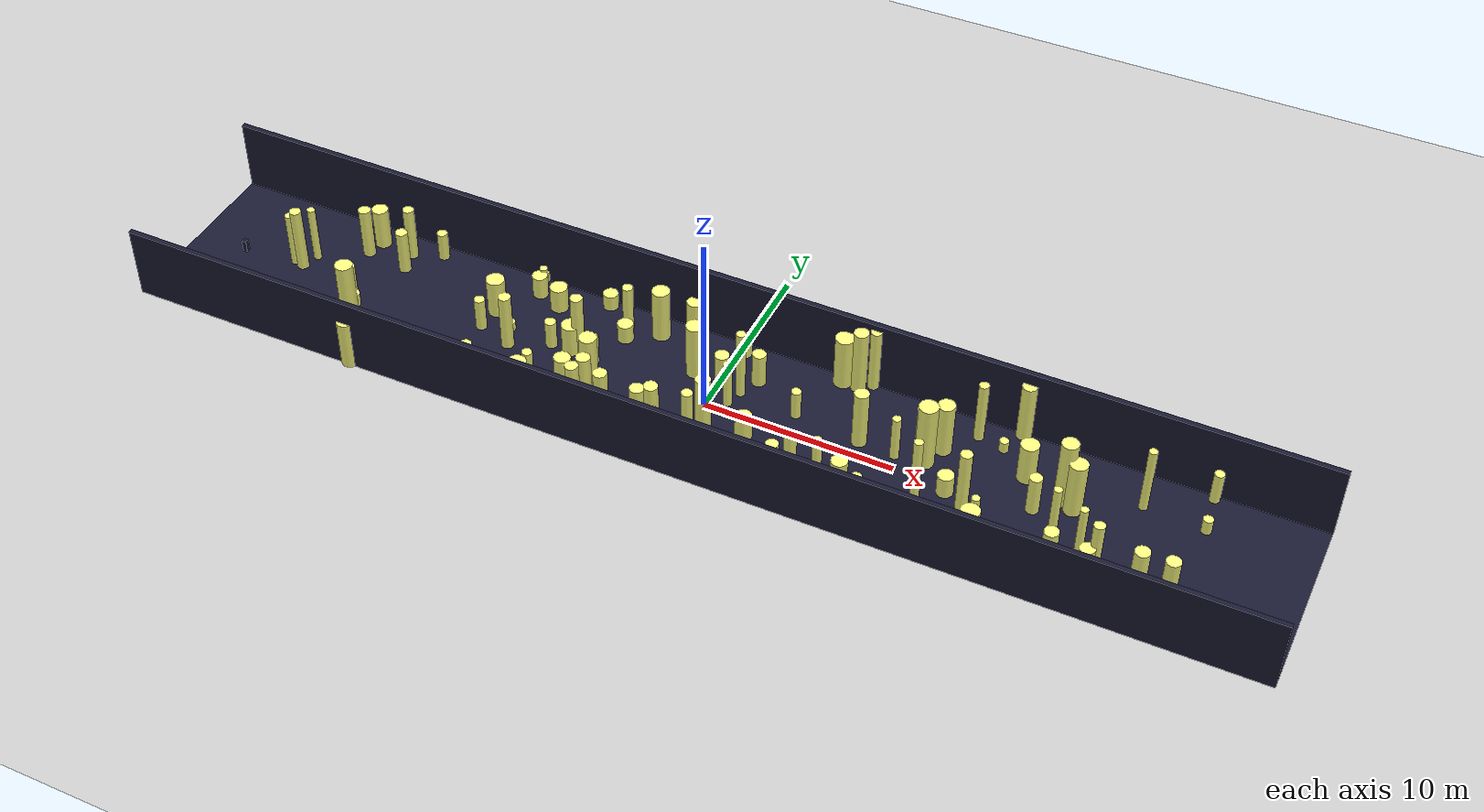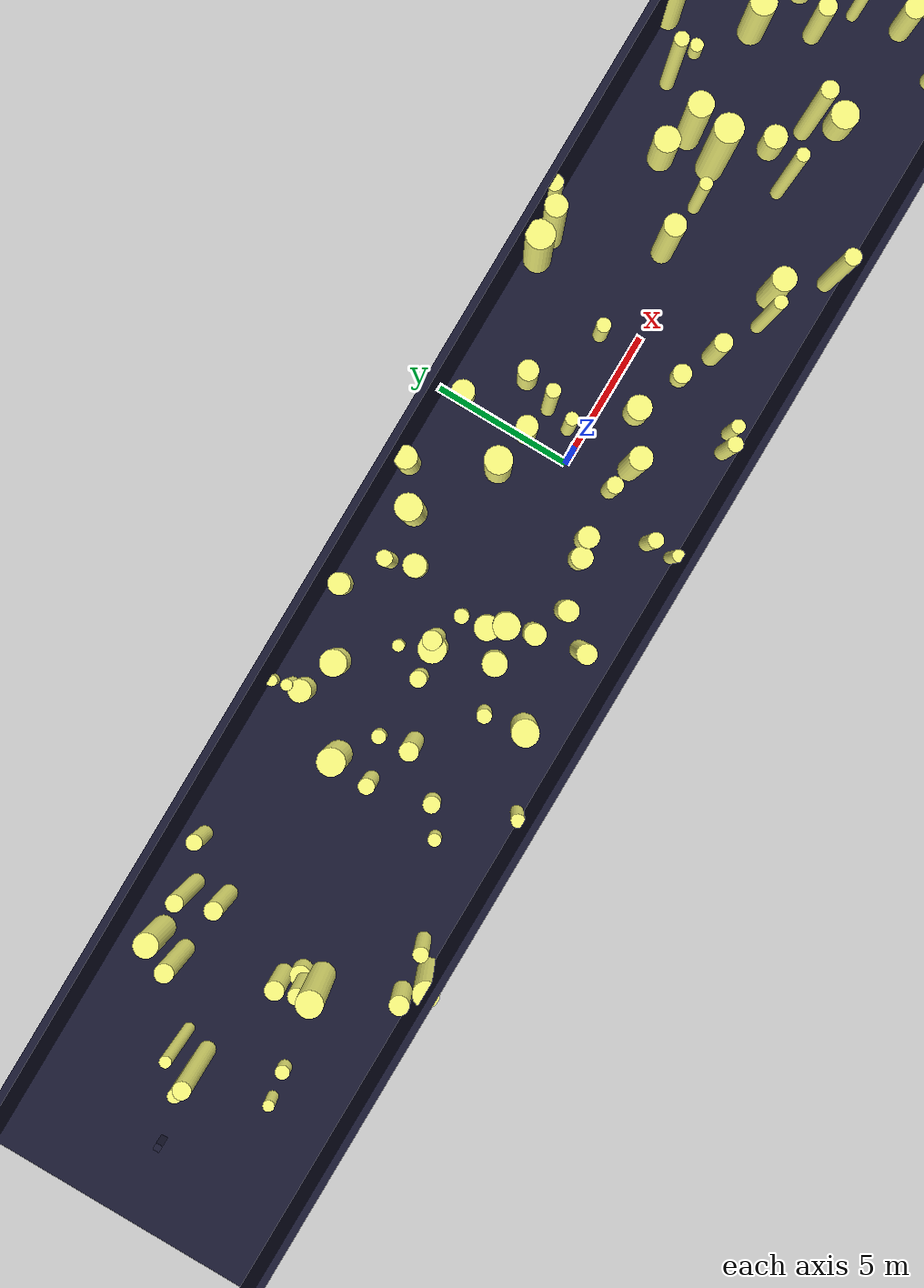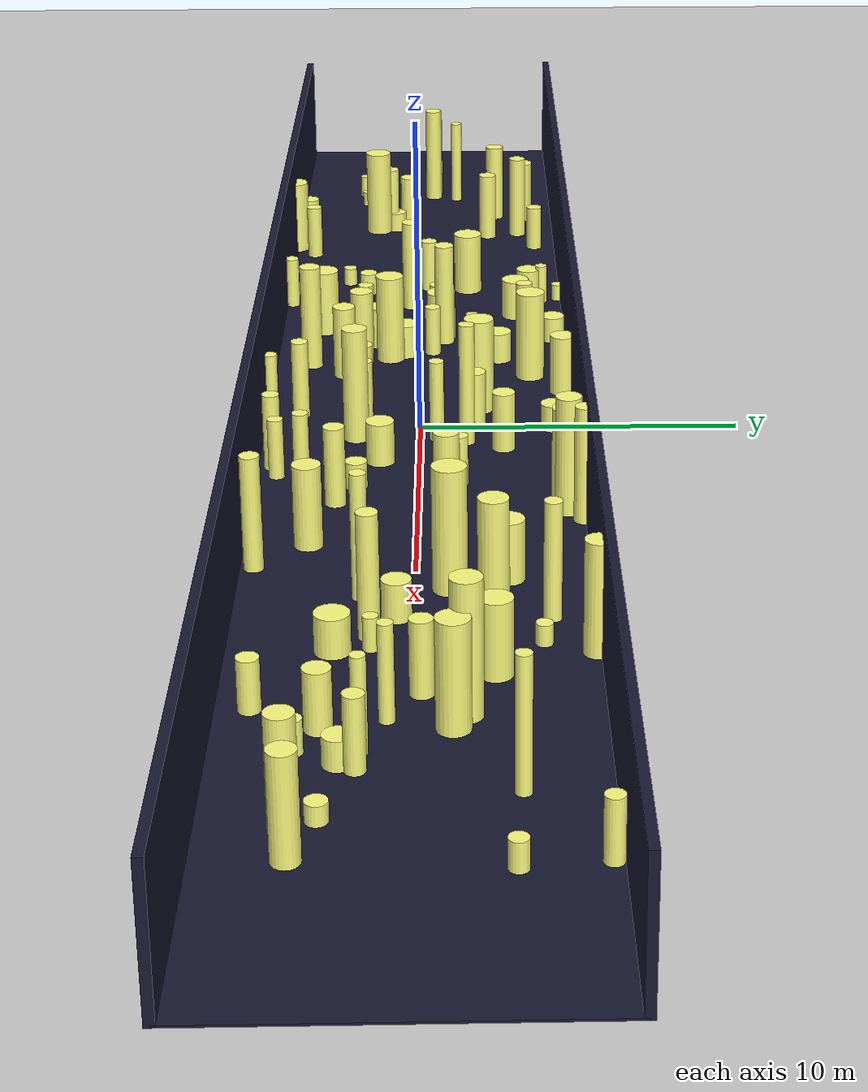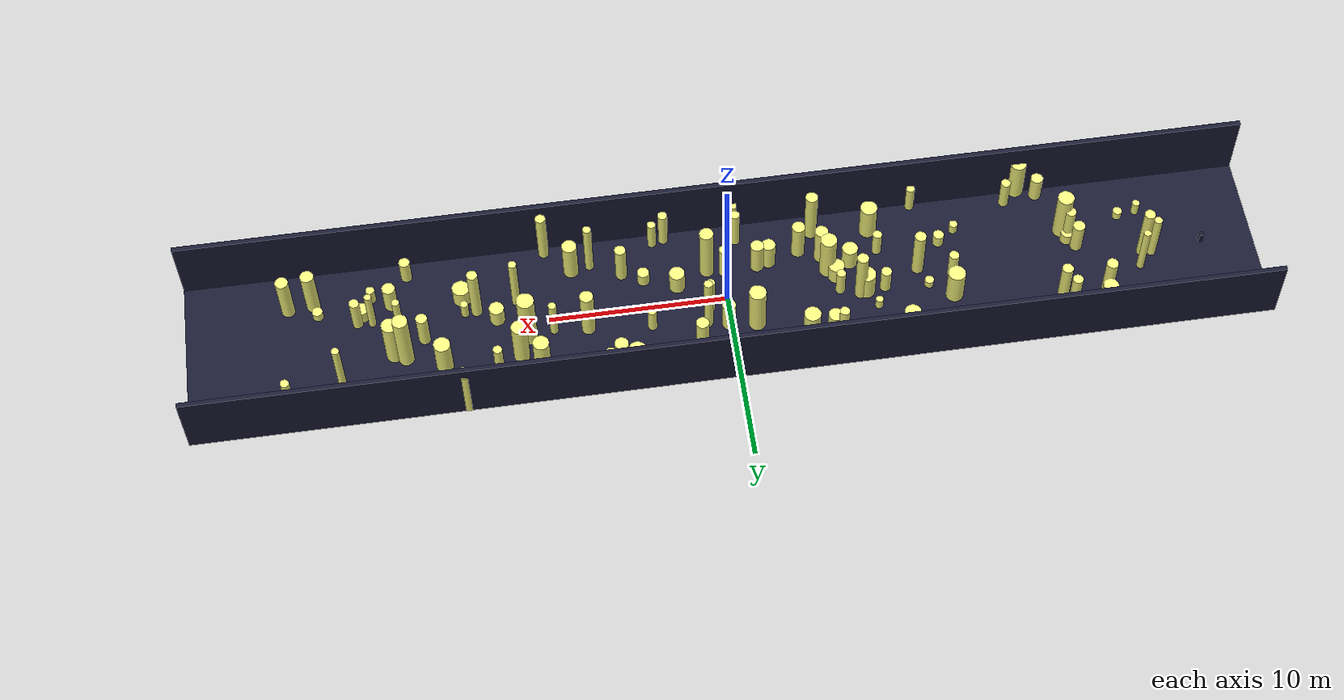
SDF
<?xml version="1.0"?>
<sdf version="1.4">
  <world name="default">
    <gui>
      <camera name="user_camera">
        <pose>-20 -30 40 0 0.66 0.83</pose>
      </camera>
    </gui>
    <include>
      <uri>model://ground_plane</uri>
    </include>
    <include>
      <uri>model://sun</uri>
    </include>
    <scene>
      <shadows>0</shadows>
    </scene>
    <model name="forest">
      <static>true</static>
      <link name="cylinder0">
        <pose>-9.830720803390115 3.235554947666131 0.7182927848972427 0 0 0 </pose>
        <visual name="visual">
          <geometry>
            <cylinder>
              <radius>0.46576942682826955</radius>
              <length>1.4365855697944854</length>
            </cylinder>
          </geometry>
          <material>
            <ambient>0.6 0.6 0.6 1</ambient>
            <diffuse>1 1 0.5 1</diffuse>
            <specular>0 0 0</specular>
            <emissive>0 0 0 1</emissive>
          </material>
        </visual>
        <collision name="collision">
          <geometry>
            <cylinder>
              <radius>0.46576942682826955</radius>
              <length>1.4365855697944854</length>
            </cylinder>
          </geometry>
          <max_contacts>0</max_contacts>
        </collision>
      </link>
      <link name="cylinder1">
        <pose>-13.301530226175817 -2.7167241906709974 0.34406534826698215 0 0 0 </pose>
        <visual name="visual">
          <geometry>
            <cylinder>
              <radius>0.23339209544105322</radius>
              <length>0.6881306965339643</length>
            </cylinder>
          </geometry>
          <material>
            <ambient>0.6 0.6 0.6 1</ambient>
            <diffuse>1 1 0.5 1</diffuse>
            <specular>0 0 0</specular>
            <emissive>0 0 0 1</emissive>
          </material>
        </visual>
        <collision name="collision">
          <geometry>
            <cylinder>
              <radius>0.23339209544105322</radius>
              <length>0.6881306965339643</length>
            </cylinder>
          </geometry>
          <max_contacts>0</max_contacts>
        </collision>
      </link>
      <link name="cylinder2">
        <pose>1.0208947712810428 0.5431389617887925 1.3426531910423 0 0 0 </pose>
        <visual name="visual">
          <geometry>
            <cylinder>
              <radius>0.22835501968407046</radius>
              <length>2.6853063820846</length>
            </cylinder>
          </geometry>
          <material>
            <ambient>0.6 0.6 0.6 1</ambient>
            <diffuse>1 1 0.5 1</diffuse>
            <specular>0 0 0</specular>
            <emissive>0 0 0 1</emissive>
          </material>
        </visual>
        <collision name="collision">
          <geometry>
            <cylinder>
              <radius>0.22835501968407046</radius>
              <length>2.6853063820846</length>
            </cylinder>
          </geometry>
          <max_contacts>0</max_contacts>
        </collision>
      </link>
      <link name="cylinder3">
        <pose>-0.9511905243909986 -3.7937651143453155 1.3032404722122595 0 0 0 </pose>
        <visual name="visual">
          <geometry>
            <cylinder>
              <radius>0.26848415864217134</radius>
              <length>2.606480944424519</length>
            </cylinder>
          </geometry>
          <material>
            <ambient>0.6 0.6 0.6 1</ambient>
            <diffuse>1 1 0.5 1</diffuse>
            <specular>0 0 0</specular>
            <emissive>0 0 0 1</emissive>
          </material>
        </visual>
        <collision name="collision">
          <geometry>
            <cylinder>
              <radius>0.26848415864217134</radius>
              <length>2.606480944424519</length>
            </cylinder>
          </geometry>
          <max_contacts>0</max_contacts>
        </collision>
      </link>
      <link name="cylinder4">
        <pose>14.357380362291096 3.42906190911415 0.33939071130231635 0 0 0 </pose>
        <visual name="visual">
          <geometry>
            <cylinder>
              <radius>0.2355430839454062</radius>
              <length>0.6787814226046327</length>
            </cylinder>
          </geometry>
          <material>
            <ambient>0.6 0.6 0.6 1</ambient>
            <diffuse>1 1 0.5 1</diffuse>
            <specular>0 0 0</specular>
            <emissive>0 0 0 1</emissive>
          </material>
        </visual>
        <collision name="collision">
          <geometry>
            <cylinder>
              <radius>0.2355430839454062</radius>
              <length>0.6787814226046327</length>
            </cylinder>
          </geometry>
          <max_contacts>0</max_contacts>
        </collision>
      </link>
      <link name="cylinder5">
        <pose>15.95672619391378 2.1406246882911226 1.1306773054959878 0 0 0 </pose>
        <visual name="visual">
          <geometry>
            <cylinder>
              <radius>0.4625027844515846</radius>
              <length>2.2613546109919755</length>
            </cylinder>
          </geometry>
          <material>
            <ambient>0.6 0.6 0.6 1</ambient>
            <diffuse>1 1 0.5 1</diffuse>
            <specular>0 0 0</specular>
            <emissive>0 0 0 1</emissive>
          </material>
        </visual>
        <collision name="collision">
          <geometry>
            <cylinder>
              <radius>0.4625027844515846</radius>
              <length>2.2613546109919755</length>
            </cylinder>
          </geometry>
          <max_contacts>0</max_contacts>
        </collision>
      </link>
      <link name="cylinder6">
        <pose>11.72142793309255 2.1433004032956973 1.518548189066716 0 0 0 </pose>
        <visual name="visual">
          <geometry>
            <cylinder>
              <radius>0.43435136117066747</radius>
              <length>3.037096378133432</length>
            </cylinder>
          </geometry>
          <material>
            <ambient>0.6 0.6 0.6 1</ambient>
            <diffuse>1 1 0.5 1</diffuse>
            <specular>0 0 0</specular>
            <emissive>0 0 0 1</emissive>
          </material>
        </visual>
        <collision name="collision">
          <geometry>
            <cylinder>
              <radius>0.43435136117066747</radius>
              <length>3.037096378133432</length>
            </cylinder>
          </geometry>
          <max_contacts>0</max_contacts>
        </collision>
      </link>
      <link name="cylinder7">
        <pose>-7.727615459679839 0.6372034440405798 0.875210409710826 0 0 0 </pose>
        <visual name="visual">
          <geometry>
            <cylinder>
              <radius>0.48508795567301455</radius>
              <length>1.750420819421652</length>
            </cylinder>
          </geometry>
          <material>
            <ambient>0.6 0.6 0.6 1</ambient>
            <diffuse>1 1 0.5 1</diffuse>
            <specular>0 0 0</specular>
            <emissive>0 0 0 1</emissive>
          </material>
        </visual>
        <collision name="collision">
          <geometry>
            <cylinder>
              <radius>0.48508795567301455</radius>
              <length>1.750420819421652</length>
            </cylinder>
          </geometry>
          <max_contacts>0</max_contacts>
        </collision>
      </link>
      <link name="cylinder8">
        <pose>19.699465234413196 -1.1801976092368216 1.3649806478278046 0 0 0 </pose>
        <visual name="visual">
          <geometry>
            <cylinder>
              <radius>0.20254438403527164</radius>
              <length>2.729961295655609</length>
            </cylinder>
          </geometry>
          <material>
            <ambient>0.6 0.6 0.6 1</ambient>
            <diffuse>1 1 0.5 1</diffuse>
            <specular>0 0 0</specular>
            <emissive>0 0 0 1</emissive>
          </material>
        </visual>
        <collision name="collision">
          <geometry>
            <cylinder>
              <radius>0.20254438403527164</radius>
              <length>2.729961295655609</length>
            </cylinder>
          </geometry>
          <max_contacts>0</max_contacts>
        </collision>
      </link>
      <link name="cylinder9">
        <pose>-17.257488566479207 4.127317122834544 0.8352382350578361 0 0 0 </pose>
        <visual name="visual">
          <geometry>
            <cylinder>
              <radius>0.2796860611333085</radius>
              <length>1.6704764701156722</length>
            </cylinder>
          </geometry>
          <material>
            <ambient>0.6 0.6 0.6 1</ambient>
            <diffuse>1 1 0.5 1</diffuse>
            <specular>0 0 0</specular>
            <emissive>0 0 0 1</emissive>
          </material>
        </visual>
        <collision name="collision">
          <geometry>
            <cylinder>
              <radius>0.2796860611333085</radius>
              <length>1.6704764701156722</length>
            </cylinder>
          </geometry>
          <max_contacts>0</max_contacts>
        </collision>
      </link>
      <link name="cylinder10">
        <pose>8.441919910510215 -3.0383918934033707 1.2916391931820514 0 0 0 </pose>
        <visual name="visual">
          <geometry>
            <cylinder>
              <radius>0.4134336815046562</radius>
              <length>2.583278386364103</length>
            </cylinder>
          </geometry>
          <material>
            <ambient>0.6 0.6 0.6 1</ambient>
            <diffuse>1 1 0.5 1</diffuse>
            <specular>0 0 0</specular>
            <emissive>0 0 0 1</emissive>
          </material>
        </visual>
        <collision name="collision">
          <geometry>
            <cylinder>
              <radius>0.4134336815046562</radius>
              <length>2.583278386364103</length>
            </cylinder>
          </geometry>
          <max_contacts>0</max_contacts>
        </collision>
      </link>
      <link name="cylinder11">
        <pose>-5.944216426440512 3.444837388084803 1.3497066958243504 0 0 0 </pose>
        <visual name="visual">
          <geometry>
            <cylinder>
              <radius>0.27424540906935424</radius>
              <length>2.699413391648701</length>
            </cylinder>
          </geometry>
          <material>
            <ambient>0.6 0.6 0.6 1</ambient>
            <diffuse>1 1 0.5 1</diffuse>
            <specular>0 0 0</specular>
            <emissive>0 0 0 1</emissive>
          </material>
        </visual>
        <collision name="collision">
          <geometry>
            <cylinder>
              <radius>0.27424540906935424</radius>
              <length>2.699413391648701</length>
            </cylinder>
          </geometry>
          <max_contacts>0</max_contacts>
        </collision>
      </link>
      <link name="cylinder12">
        <pose>24.27517334014935 -2.6602131412921546 1.470125046250434 0 0 0 </pose>
        <visual name="visual">
          <geometry>
            <cylinder>
              <radius>0.36455640942420675</radius>
              <length>2.940250092500868</length>
            </cylinder>
          </geometry>
          <material>
            <ambient>0.6 0.6 0.6 1</ambient>
            <diffuse>1 1 0.5 1</diffuse>
            <specular>0 0 0</specular>
            <emissive>0 0 0 1</emissive>
          </material>
        </visual>
        <collision name="collision">
          <geometry>
            <cylinder>
              <radius>0.36455640942420675</radius>
              <length>2.940250092500868</length>
            </cylinder>
          </geometry>
          <max_contacts>0</max_contacts>
        </collision>
      </link>
      <link name="cylinder13">
        <pose>-12.561981277283774 1.5787413002267412 1.1028347483679917 0 0 0 </pose>
        <visual name="visual">
          <geometry>
            <cylinder>
              <radius>0.48482916464376824</radius>
              <length>2.2056694967359833</length>
            </cylinder>
          </geometry>
          <material>
            <ambient>0.6 0.6 0.6 1</ambient>
            <diffuse>1 1 0.5 1</diffuse>
            <specular>0 0 0</specular>
            <emissive>0 0 0 1</emissive>
          </material>
        </visual>
        <collision name="collision">
          <geometry>
            <cylinder>
              <radius>0.48482916464376824</radius>
              <length>2.2056694967359833</length>
            </cylinder>
          </geometry>
          <max_contacts>0</max_contacts>
        </collision>
      </link>
      <link name="cylinder14">
        <pose>22.65406599161711 -2.0612876650250778 0.30610132249239846 0 0 0 </pose>
        <visual name="visual">
          <geometry>
            <cylinder>
              <radius>0.2918572696765596</radius>
              <length>0.6122026449847969</length>
            </cylinder>
          </geometry>
          <material>
            <ambient>0.6 0.6 0.6 1</ambient>
            <diffuse>1 1 0.5 1</diffuse>
            <specular>0 0 0</specular>
            <emissive>0 0 0 1</emissive>
          </material>
        </visual>
        <collision name="collision">
          <geometry>
            <cylinder>
              <radius>0.2918572696765596</radius>
              <length>0.6122026449847969</length>
            </cylinder>
          </geometry>
          <max_contacts>0</max_contacts>
        </collision>
      </link>
      <link name="cylinder15">
        <pose>-5.663796459011827 2.5820999626042065 0.5426901355455794 0 0 0 </pose>
        <visual name="visual">
          <geometry>
            <cylinder>
              <radius>0.41271997819827655</radius>
              <length>1.0853802710911589</length>
            </cylinder>
          </geometry>
          <material>
            <ambient>0.6 0.6 0.6 1</ambient>
            <diffuse>1 1 0.5 1</diffuse>
            <specular>0 0 0</specular>
            <emissive>0 0 0 1</emissive>
          </material>
        </visual>
        <collision name="collision">
          <geometry>
            <cylinder>
              <radius>0.41271997819827655</radius>
              <length>1.0853802710911589</length>
            </cylinder>
          </geometry>
          <max_contacts>0</max_contacts>
        </collision>
      </link>
      <link name="cylinder16">
        <pose>-18.83287300930011 3.522302612712915 1.558999867058374 0 0 0 </pose>
        <visual name="visual">
          <geometry>
            <cylinder>
              <radius>0.2926893200501962</radius>
              <length>3.117999734116748</length>
            </cylinder>
          </geometry>
          <material>
            <ambient>0.6 0.6 0.6 1</ambient>
            <diffuse>1 1 0.5 1</diffuse>
            <specular>0 0 0</specular>
            <emissive>0 0 0 1</emissive>
          </material>
        </visual>
        <collision name="collision">
          <geometry>
            <cylinder>
              <radius>0.2926893200501962</radius>
              <length>3.117999734116748</length>
            </cylinder>
          </geometry>
          <max_contacts>0</max_contacts>
        </collision>
      </link>
      <link name="cylinder17">
        <pose>-0.964448442852671 -4.726974164393326 1.0846007019325463 0 0 0 </pose>
        <visual name="visual">
          <geometry>
            <cylinder>
              <radius>0.21282826584180448</radius>
              <length>2.1692014038650926</length>
            </cylinder>
          </geometry>
          <material>
            <ambient>0.6 0.6 0.6 1</ambient>
            <diffuse>1 1 0.5 1</diffuse>
            <specular>0 0 0</specular>
            <emissive>0 0 0 1</emissive>
          </material>
        </visual>
        <collision name="collision">
          <geometry>
            <cylinder>
              <radius>0.21282826584180448</radius>
              <length>2.1692014038650926</length>
            </cylinder>
          </geometry>
          <max_contacts>0</max_contacts>
        </collision>
      </link>
      <link name="cylinder18">
        <pose>17.615794449780587 -3.985222112901603 0.7751889481892782 0 0 0 </pose>
        <visual name="visual">
          <geometry>
            <cylinder>
              <radius>0.30276084775036843</radius>
              <length>1.5503778963785564</length>
            </cylinder>
          </geometry>
          <material>
            <ambient>0.6 0.6 0.6 1</ambient>
            <diffuse>1 1 0.5 1</diffuse>
            <specular>0 0 0</specular>
            <emissive>0 0 0 1</emissive>
          </material>
        </visual>
        <collision name="collision">
          <geometry>
            <cylinder>
              <radius>0.30276084775036843</radius>
              <length>1.5503778963785564</length>
            </cylinder>
          </geometry>
          <max_contacts>0</max_contacts>
        </collision>
      </link>
      <link name="cylinder19">
        <pose>-7.485077178065264 4.46773874166276 0.47083643337854875 0 0 0 </pose>
        <visual name="visual">
          <geometry>
            <cylinder>
              <radius>0.3938477574909951</radius>
              <length>0.9416728667570975</length>
            </cylinder>
          </geometry>
          <material>
            <ambient>0.6 0.6 0.6 1</ambient>
            <diffuse>1 1 0.5 1</diffuse>
            <specular>0 0 0</specular>
            <emissive>0 0 0 1</emissive>
          </material>
        </visual>
        <collision name="collision">
          <geometry>
            <cylinder>
              <radius>0.3938477574909951</radius>
              <length>0.9416728667570975</length>
            </cylinder>
          </geometry>
          <max_contacts>0</max_contacts>
        </collision>
      </link>
      <link name="cylinder20">
        <pose>24.43067726238239 4.62530078184065 0.8967429362178146 0 0 0 </pose>
        <visual name="visual">
          <geometry>
            <cylinder>
              <radius>0.25407514421779676</radius>
              <length>1.7934858724356293</length>
            </cylinder>
          </geometry>
          <material>
            <ambient>0.6 0.6 0.6 1</ambient>
            <diffuse>1 1 0.5 1</diffuse>
            <specular>0 0 0</specular>
            <emissive>0 0 0 1</emissive>
          </material>
        </visual>
        <collision name="collision">
          <geometry>
            <cylinder>
              <radius>0.25407514421779676</radius>
              <length>1.7934858724356293</length>
            </cylinder>
          </geometry>
          <max_contacts>0</max_contacts>
        </collision>
      </link>
      <link name="cylinder21">
        <pose>24.65642489110388 2.5068368066967732 0.4347260987845433 0 0 0 </pose>
        <visual name="visual">
          <geometry>
            <cylinder>
              <radius>0.25245440863690455</radius>
              <length>0.8694521975690866</length>
            </cylinder>
          </geometry>
          <material>
            <ambient>0.6 0.6 0.6 1</ambient>
            <diffuse>1 1 0.5 1</diffuse>
            <specular>0 0 0</specular>
            <emissive>0 0 0 1</emissive>
          </material>
        </visual>
        <collision name="collision">
          <geometry>
            <cylinder>
              <radius>0.25245440863690455</radius>
              <length>0.8694521975690866</length>
            </cylinder>
          </geometry>
          <max_contacts>0</max_contacts>
        </collision>
      </link>
      <link name="cylinder22">
        <pose>-6.304854473788968 0.3614920475337824 0.8680897214315368 0 0 0 </pose>
        <visual name="visual">
          <geometry>
            <cylinder>
              <radius>0.2554054732506064</radius>
              <length>1.7361794428630737</length>
            </cylinder>
          </geometry>
          <material>
            <ambient>0.6 0.6 0.6 1</ambient>
            <diffuse>1 1 0.5 1</diffuse>
            <specular>0 0 0</specular>
            <emissive>0 0 0 1</emissive>
          </material>
        </visual>
        <collision name="collision">
          <geometry>
            <cylinder>
              <radius>0.2554054732506064</radius>
              <length>1.7361794428630737</length>
            </cylinder>
          </geometry>
          <max_contacts>0</max_contacts>
        </collision>
      </link>
      <link name="cylinder23">
        <pose>-11.13874105460969 -4.690529326969451 0.9060957126560065 0 0 0 </pose>
        <visual name="visual">
          <geometry>
            <cylinder>
              <radius>0.23863124001657485</radius>
              <length>1.812191425312013</length>
            </cylinder>
          </geometry>
          <material>
            <ambient>0.6 0.6 0.6 1</ambient>
            <diffuse>1 1 0.5 1</diffuse>
            <specular>0 0 0</specular>
            <emissive>0 0 0 1</emissive>
          </material>
        </visual>
        <collision name="collision">
          <geometry>
            <cylinder>
              <radius>0.23863124001657485</radius>
              <length>1.812191425312013</length>
            </cylinder>
          </geometry>
          <max_contacts>0</max_contacts>
        </collision>
      </link>
      <link name="cylinder24">
        <pose>-6.215196501369231 -0.5662569450970292 0.5940139332361044 0 0 0 </pose>
        <visual name="visual">
          <geometry>
            <cylinder>
              <radius>0.4460458054168145</radius>
              <length>1.1880278664722088</length>
            </cylinder>
          </geometry>
          <material>
            <ambient>0.6 0.6 0.6 1</ambient>
            <diffuse>1 1 0.5 1</diffuse>
            <specular>0 0 0</specular>
            <emissive>0 0 0 1</emissive>
          </material>
        </visual>
        <collision name="collision">
          <geometry>
            <cylinder>
              <radius>0.4460458054168145</radius>
              <length>1.1880278664722088</length>
            </cylinder>
          </geometry>
          <max_contacts>0</max_contacts>
        </collision>
      </link>
      <link name="cylinder25">
        <pose>16.9242625028197 0.27205600537427177 1.1013196231043145 0 0 0 </pose>
        <visual name="visual">
          <geometry>
            <cylinder>
              <radius>0.3196346392363912</radius>
              <length>2.202639246208629</length>
            </cylinder>
          </geometry>
          <material>
            <ambient>0.6 0.6 0.6 1</ambient>
            <diffuse>1 1 0.5 1</diffuse>
            <specular>0 0 0</specular>
            <emissive>0 0 0 1</emissive>
          </material>
        </visual>
        <collision name="collision">
          <geometry>
            <cylinder>
              <radius>0.3196346392363912</radius>
              <length>2.202639246208629</length>
            </cylinder>
          </geometry>
          <max_contacts>0</max_contacts>
        </collision>
      </link>
      <link name="cylinder26">
        <pose>-23.807733474724664 -2.4915112711571306 0.45131721621917525 0 0 0 </pose>
        <visual name="visual">
          <geometry>
            <cylinder>
              <radius>0.2038216445307513</radius>
              <length>0.9026344324383505</length>
            </cylinder>
          </geometry>
          <material>
            <ambient>0.6 0.6 0.6 1</ambient>
            <diffuse>1 1 0.5 1</diffuse>
            <specular>0 0 0</specular>
            <emissive>0 0 0 1</emissive>
          </material>
        </visual>
        <collision name="collision">
          <geometry>
            <cylinder>
              <radius>0.2038216445307513</radius>
              <length>0.9026344324383505</length>
            </cylinder>
          </geometry>
          <max_contacts>0</max_contacts>
        </collision>
      </link>
      <link name="cylinder27">
        <pose>1.766755526100173 2.604636848300447 0.9732648832684428 0 0 0 </pose>
        <visual name="visual">
          <geometry>
            <cylinder>
              <radius>0.35749040720921466</radius>
              <length>1.9465297665368857</length>
            </cylinder>
          </geometry>
          <material>
            <ambient>0.6 0.6 0.6 1</ambient>
            <diffuse>1 1 0.5 1</diffuse>
            <specular>0 0 0</specular>
            <emissive>0 0 0 1</emissive>
          </material>
        </visual>
        <collision name="collision">
          <geometry>
            <cylinder>
              <radius>0.35749040720921466</radius>
              <length>1.9465297665368857</length>
            </cylinder>
          </geometry>
          <max_contacts>0</max_contacts>
        </collision>
      </link>
      <link name="cylinder28">
        <pose>22.880518140336733 -2.802426067439696 1.5214850839309941 0 0 0 </pose>
        <visual name="visual">
          <geometry>
            <cylinder>
              <radius>0.3747662969486343</radius>
              <length>3.0429701678619883</length>
            </cylinder>
          </geometry>
          <material>
            <ambient>0.6 0.6 0.6 1</ambient>
            <diffuse>1 1 0.5 1</diffuse>
            <specular>0 0 0</specular>
            <emissive>0 0 0 1</emissive>
          </material>
        </visual>
        <collision name="collision">
          <geometry>
            <cylinder>
              <radius>0.3747662969486343</radius>
              <length>3.0429701678619883</length>
            </cylinder>
          </geometry>
          <max_contacts>0</max_contacts>
        </collision>
      </link>
      <link name="cylinder29">
        <pose>14.892574944241282 4.791217000073189 1.6624655020170058 0 0 0 </pose>
        <visual name="visual">
          <geometry>
            <cylinder>
              <radius>0.38092229612289386</radius>
              <length>3.3249310040340117</length>
            </cylinder>
          </geometry>
          <material>
            <ambient>0.6 0.6 0.6 1</ambient>
            <diffuse>1 1 0.5 1</diffuse>
            <specular>0 0 0</specular>
            <emissive>0 0 0 1</emissive>
          </material>
        </visual>
        <collision name="collision">
          <geometry>
            <cylinder>
              <radius>0.38092229612289386</radius>
              <length>3.3249310040340117</length>
            </cylinder>
          </geometry>
          <max_contacts>0</max_contacts>
        </collision>
      </link>
      <link name="cylinder30">
        <pose>-1.3838550974502368 1.8779981275210158 1.5812145388326357 0 0 0 </pose>
        <visual name="visual">
          <geometry>
            <cylinder>
              <radius>0.47093085014604186</radius>
              <length>3.1624290776652715</length>
            </cylinder>
          </geometry>
          <material>
            <ambient>0.6 0.6 0.6 1</ambient>
            <diffuse>1 1 0.5 1</diffuse>
            <specular>0 0 0</specular>
            <emissive>0 0 0 1</emissive>
          </material>
        </visual>
        <collision name="collision">
          <geometry>
            <cylinder>
              <radius>0.47093085014604186</radius>
              <length>3.1624290776652715</length>
            </cylinder>
          </geometry>
          <max_contacts>0</max_contacts>
        </collision>
      </link>
      <link name="cylinder31">
        <pose>5.52481053012815 4.436602579123484 1.4965811906015696 0 0 0 </pose>
        <visual name="visual">
          <geometry>
            <cylinder>
              <radius>0.4910310022509187</radius>
              <length>2.993162381203139</length>
            </cylinder>
          </geometry>
          <material>
            <ambient>0.6 0.6 0.6 1</ambient>
            <diffuse>1 1 0.5 1</diffuse>
            <specular>0 0 0</specular>
            <emissive>0 0 0 1</emissive>
          </material>
        </visual>
        <collision name="collision">
          <geometry>
            <cylinder>
              <radius>0.4910310022509187</radius>
              <length>2.993162381203139</length>
            </cylinder>
          </geometry>
          <max_contacts>0</max_contacts>
        </collision>
      </link>
      <link name="cylinder32">
        <pose>10.638708478671752 2.5784878070132837 0.9510251556961719 0 0 0 </pose>
        <visual name="visual">
          <geometry>
            <cylinder>
              <radius>0.4526687696213297</radius>
              <length>1.9020503113923437</length>
            </cylinder>
          </geometry>
          <material>
            <ambient>0.6 0.6 0.6 1</ambient>
            <diffuse>1 1 0.5 1</diffuse>
            <specular>0 0 0</specular>
            <emissive>0 0 0 1</emissive>
          </material>
        </visual>
        <collision name="collision">
          <geometry>
            <cylinder>
              <radius>0.4526687696213297</radius>
              <length>1.9020503113923437</length>
            </cylinder>
          </geometry>
          <max_contacts>0</max_contacts>
        </collision>
      </link>
      <link name="cylinder33">
        <pose>-8.49420739531984 -3.3857336237281856 1.1487312700447918 0 0 0 </pose>
        <visual name="visual">
          <geometry>
            <cylinder>
              <radius>0.4723207564353888</radius>
              <length>2.2974625400895836</length>
            </cylinder>
          </geometry>
          <material>
            <ambient>0.6 0.6 0.6 1</ambient>
            <diffuse>1 1 0.5 1</diffuse>
            <specular>0 0 0</specular>
            <emissive>0 0 0 1</emissive>
          </material>
        </visual>
        <collision name="collision">
          <geometry>
            <cylinder>
              <radius>0.4723207564353888</radius>
              <length>2.2974625400895836</length>
            </cylinder>
          </geometry>
          <max_contacts>0</max_contacts>
        </collision>
      </link>
      <link name="cylinder34">
        <pose>-19.61475089470376 -1.3592354045587038 1.2410937346082427 0 0 0 </pose>
        <visual name="visual">
          <geometry>
            <cylinder>
              <radius>0.2944435240690829</radius>
              <length>2.4821874692164854</length>
            </cylinder>
          </geometry>
          <material>
            <ambient>0.6 0.6 0.6 1</ambient>
            <diffuse>1 1 0.5 1</diffuse>
            <specular>0 0 0</specular>
            <emissive>0 0 0 1</emissive>
          </material>
        </visual>
        <collision name="collision">
          <geometry>
            <cylinder>
              <radius>0.2944435240690829</radius>
              <length>2.4821874692164854</length>
            </cylinder>
          </geometry>
          <max_contacts>0</max_contacts>
        </collision>
      </link>
      <link name="cylinder35">
        <pose>-5.2605845754147005 -3.674934649735201 1.7868303058974122 0 0 0 </pose>
        <visual name="visual">
          <geometry>
            <cylinder>
              <radius>0.3398801913396128</radius>
              <length>3.5736606117948244</length>
            </cylinder>
          </geometry>
          <material>
            <ambient>0.6 0.6 0.6 1</ambient>
            <diffuse>1 1 0.5 1</diffuse>
            <specular>0 0 0</specular>
            <emissive>0 0 0 1</emissive>
          </material>
        </visual>
        <collision name="collision">
          <geometry>
            <cylinder>
              <radius>0.3398801913396128</radius>
              <length>3.5736606117948244</length>
            </cylinder>
          </geometry>
          <max_contacts>0</max_contacts>
        </collision>
      </link>
      <link name="cylinder36">
        <pose>9.842615635344423 -4.4811699380795025 1.7462603156904977 0 0 0 </pose>
        <visual name="visual">
          <geometry>
            <cylinder>
              <radius>0.2838949741445699</radius>
              <length>3.4925206313809953</length>
            </cylinder>
          </geometry>
          <material>
            <ambient>0.6 0.6 0.6 1</ambient>
            <diffuse>1 1 0.5 1</diffuse>
            <specular>0 0 0</specular>
            <emissive>0 0 0 1</emissive>
          </material>
        </visual>
        <collision name="collision">
          <geometry>
            <cylinder>
              <radius>0.2838949741445699</radius>
              <length>3.4925206313809953</length>
            </cylinder>
          </geometry>
          <max_contacts>0</max_contacts>
        </collision>
      </link>
      <link name="cylinder37">
        <pose>-19.350280301945293 -1.8211270992761386 1.6157213406520552 0 0 0 </pose>
        <visual name="visual">
          <geometry>
            <cylinder>
              <radius>0.46232408937305763</radius>
              <length>3.2314426813041104</length>
            </cylinder>
          </geometry>
          <material>
            <ambient>0.6 0.6 0.6 1</ambient>
            <diffuse>1 1 0.5 1</diffuse>
            <specular>0 0 0</specular>
            <emissive>0 0 0 1</emissive>
          </material>
        </visual>
        <collision name="collision">
          <geometry>
            <cylinder>
              <radius>0.46232408937305763</radius>
              <length>3.2314426813041104</length>
            </cylinder>
          </geometry>
          <max_contacts>0</max_contacts>
        </collision>
      </link>
      <link name="cylinder38">
        <pose>-20.73963934576656 3.6914156899435504 1.1835903976359519 0 0 0 </pose>
        <visual name="visual">
          <geometry>
            <cylinder>
              <radius>0.428591396780448</radius>
              <length>2.3671807952719037</length>
            </cylinder>
          </geometry>
          <material>
            <ambient>0.6 0.6 0.6 1</ambient>
            <diffuse>1 1 0.5 1</diffuse>
            <specular>0 0 0</specular>
            <emissive>0 0 0 1</emissive>
          </material>
        </visual>
        <collision name="collision">
          <geometry>
            <cylinder>
              <radius>0.428591396780448</radius>
              <length>2.3671807952719037</length>
            </cylinder>
          </geometry>
          <max_contacts>0</max_contacts>
        </collision>
      </link>
      <link name="cylinder39">
        <pose>-1.9350343566588037 -1.8985625384711327 1.046354484008154 0 0 0 </pose>
        <visual name="visual">
          <geometry>
            <cylinder>
              <radius>0.3694459770511317</radius>
              <length>2.092708968016308</length>
            </cylinder>
          </geometry>
          <material>
            <ambient>0.6 0.6 0.6 1</ambient>
            <diffuse>1 1 0.5 1</diffuse>
            <specular>0 0 0</specular>
            <emissive>0 0 0 1</emissive>
          </material>
        </visual>
        <collision name="collision">
          <geometry>
            <cylinder>
              <radius>0.3694459770511317</radius>
              <length>2.092708968016308</length>
            </cylinder>
          </geometry>
          <max_contacts>0</max_contacts>
        </collision>
      </link>
      <link name="cylinder40">
        <pose>9.787444862353858 0.7200216689745194 1.284834258719329 0 0 0 </pose>
        <visual name="visual">
          <geometry>
            <cylinder>
              <radius>0.22169944320740143</radius>
              <length>2.569668517438658</length>
            </cylinder>
          </geometry>
          <material>
            <ambient>0.6 0.6 0.6 1</ambient>
            <diffuse>1 1 0.5 1</diffuse>
            <specular>0 0 0</specular>
            <emissive>0 0 0 1</emissive>
          </material>
        </visual>
        <collision name="collision">
          <geometry>
            <cylinder>
              <radius>0.22169944320740143</radius>
              <length>2.569668517438658</length>
            </cylinder>
          </geometry>
          <max_contacts>0</max_contacts>
        </collision>
      </link>
      <link name="cylinder41">
        <pose>-11.285041992487487 0.695047360578612 0.26740590351343896 0 0 0 </pose>
        <visual name="visual">
          <geometry>
            <cylinder>
              <radius>0.25663282416869626</radius>
              <length>0.5348118070268779</length>
            </cylinder>
          </geometry>
          <material>
            <ambient>0.6 0.6 0.6 1</ambient>
            <diffuse>1 1 0.5 1</diffuse>
            <specular>0 0 0</specular>
            <emissive>0 0 0 1</emissive>
          </material>
        </visual>
        <collision name="collision">
          <geometry>
            <cylinder>
              <radius>0.25663282416869626</radius>
              <length>0.5348118070268779</length>
            </cylinder>
          </geometry>
          <max_contacts>0</max_contacts>
        </collision>
      </link>
      <link name="cylinder42">
        <pose>19.651748811338408 -2.774950141528473 0.5063509401220356 0 0 0 </pose>
        <visual name="visual">
          <geometry>
            <cylinder>
              <radius>0.24487150854859474</radius>
              <length>1.0127018802440713</length>
            </cylinder>
          </geometry>
          <material>
            <ambient>0.6 0.6 0.6 1</ambient>
            <diffuse>1 1 0.5 1</diffuse>
            <specular>0 0 0</specular>
            <emissive>0 0 0 1</emissive>
          </material>
        </visual>
        <collision name="collision">
          <geometry>
            <cylinder>
              <radius>0.24487150854859474</radius>
              <length>1.0127018802440713</length>
            </cylinder>
          </geometry>
          <max_contacts>0</max_contacts>
        </collision>
      </link>
      <link name="cylinder43">
        <pose>-4.13885723590392 3.5897968480393914 1.516773556248452 0 0 0 </pose>
        <visual name="visual">
          <geometry>
            <cylinder>
              <radius>0.4613242985159272</radius>
              <length>3.033547112496904</length>
            </cylinder>
          </geometry>
          <material>
            <ambient>0.6 0.6 0.6 1</ambient>
            <diffuse>1 1 0.5 1</diffuse>
            <specular>0 0 0</specular>
            <emissive>0 0 0 1</emissive>
          </material>
        </visual>
        <collision name="collision">
          <geometry>
            <cylinder>
              <radius>0.4613242985159272</radius>
              <length>3.033547112496904</length>
            </cylinder>
          </geometry>
          <max_contacts>0</max_contacts>
        </collision>
      </link>
      <link name="cylinder44">
        <pose>3.053273287268542 -4.424035636804914 1.2382240117531607 0 0 0 </pose>
        <visual name="visual">
          <geometry>
            <cylinder>
              <radius>0.2646642352338189</radius>
              <length>2.4764480235063213</length>
            </cylinder>
          </geometry>
          <material>
            <ambient>0.6 0.6 0.6 1</ambient>
            <diffuse>1 1 0.5 1</diffuse>
            <specular>0 0 0</specular>
            <emissive>0 0 0 1</emissive>
          </material>
        </visual>
        <collision name="collision">
          <geometry>
            <cylinder>
              <radius>0.2646642352338189</radius>
              <length>2.4764480235063213</length>
            </cylinder>
          </geometry>
          <max_contacts>0</max_contacts>
        </collision>
      </link>
      <link name="cylinder45">
        <pose>21.557904494474514 2.6938805515932573 1.8765536206004654 0 0 0 </pose>
        <visual name="visual">
          <geometry>
            <cylinder>
              <radius>0.21237045270549917</radius>
              <length>3.7531072412009308</length>
            </cylinder>
          </geometry>
          <material>
            <ambient>0.6 0.6 0.6 1</ambient>
            <diffuse>1 1 0.5 1</diffuse>
            <specular>0 0 0</specular>
            <emissive>0 0 0 1</emissive>
          </material>
        </visual>
        <collision name="collision">
          <geometry>
            <cylinder>
              <radius>0.21237045270549917</radius>
              <length>3.7531072412009308</length>
            </cylinder>
          </geometry>
          <max_contacts>0</max_contacts>
        </collision>
      </link>
      <link name="cylinder46">
        <pose>6.371458550900872 4.3896777458545575 1.8508873952760432 0 0 0 </pose>
        <visual name="visual">
          <geometry>
            <cylinder>
              <radius>0.38006477681204065</radius>
              <length>3.7017747905520864</length>
            </cylinder>
          </geometry>
          <material>
            <ambient>0.6 0.6 0.6 1</ambient>
            <diffuse>1 1 0.5 1</diffuse>
            <specular>0 0 0</specular>
            <emissive>0 0 0 1</emissive>
          </material>
        </visual>
        <collision name="collision">
          <geometry>
            <cylinder>
              <radius>0.38006477681204065</radius>
              <length>3.7017747905520864</length>
            </cylinder>
          </geometry>
          <max_contacts>0</max_contacts>
        </collision>
      </link>
      <link name="cylinder47">
        <pose>-8.275534236177794 1.699405641100081 0.3616090841700658 0 0 0 </pose>
        <visual name="visual">
          <geometry>
            <cylinder>
              <radius>0.2134403789157707</radius>
              <length>0.7232181683401316</length>
            </cylinder>
          </geometry>
          <material>
            <ambient>0.6 0.6 0.6 1</ambient>
            <diffuse>1 1 0.5 1</diffuse>
            <specular>0 0 0</specular>
            <emissive>0 0 0 1</emissive>
          </material>
        </visual>
        <collision name="collision">
          <geometry>
            <cylinder>
              <radius>0.2134403789157707</radius>
              <length>0.7232181683401316</length>
            </cylinder>
          </geometry>
          <max_contacts>0</max_contacts>
        </collision>
      </link>
      <link name="cylinder48">
        <pose>-7.11029083336016 -1.401633446989047 0.7380359977490331 0 0 0 </pose>
        <visual name="visual">
          <geometry>
            <cylinder>
              <radius>0.43815324421603563</radius>
              <length>1.4760719954980661</length>
            </cylinder>
          </geometry>
          <material>
            <ambient>0.6 0.6 0.6 1</ambient>
            <diffuse>1 1 0.5 1</diffuse>
            <specular>0 0 0</specular>
            <emissive>0 0 0 1</emissive>
          </material>
        </visual>
        <collision name="collision">
          <geometry>
            <cylinder>
              <radius>0.43815324421603563</radius>
              <length>1.4760719954980661</length>
            </cylinder>
          </geometry>
          <max_contacts>0</max_contacts>
        </collision>
      </link>
      <link name="cylinder49">
        <pose>0.9077108083964127 -1.9675311596262701 1.8729571938885456 0 0 0 </pose>
        <visual name="visual">
          <geometry>
            <cylinder>
              <radius>0.38956717314669087</radius>
              <length>3.7459143877770913</length>
            </cylinder>
          </geometry>
          <material>
            <ambient>0.6 0.6 0.6 1</ambient>
            <diffuse>1 1 0.5 1</diffuse>
            <specular>0 0 0</specular>
            <emissive>0 0 0 1</emissive>
          </material>
        </visual>
        <collision name="collision">
          <geometry>
            <cylinder>
              <radius>0.38956717314669087</radius>
              <length>3.7459143877770913</length>
            </cylinder>
          </geometry>
          <max_contacts>0</max_contacts>
        </collision>
      </link>
      <link name="cylinder50">
        <pose>20.22069144145675 -1.6902316473149193 0.4480826638899943 0 0 0 </pose>
        <visual name="visual">
          <geometry>
            <cylinder>
              <radius>0.3896147406914823</radius>
              <length>0.8961653277799886</length>
            </cylinder>
          </geometry>
          <material>
            <ambient>0.6 0.6 0.6 1</ambient>
            <diffuse>1 1 0.5 1</diffuse>
            <specular>0 0 0</specular>
            <emissive>0 0 0 1</emissive>
          </material>
        </visual>
        <collision name="collision">
          <geometry>
            <cylinder>
              <radius>0.3896147406914823</radius>
              <length>0.8961653277799886</length>
            </cylinder>
          </geometry>
          <max_contacts>0</max_contacts>
        </collision>
      </link>
      <link name="cylinder51">
        <pose>-5.57228291579494 -2.000016582609586 1.295378873262297 0 0 0 </pose>
        <visual name="visual">
          <geometry>
            <cylinder>
              <radius>0.37143090009585644</radius>
              <length>2.590757746524594</length>
            </cylinder>
          </geometry>
          <material>
            <ambient>0.6 0.6 0.6 1</ambient>
            <diffuse>1 1 0.5 1</diffuse>
            <specular>0 0 0</specular>
            <emissive>0 0 0 1</emissive>
          </material>
        </visual>
        <collision name="collision">
          <geometry>
            <cylinder>
              <radius>0.37143090009585644</radius>
              <length>2.590757746524594</length>
            </cylinder>
          </geometry>
          <max_contacts>0</max_contacts>
        </collision>
      </link>
      <link name="cylinder52">
        <pose>13.91282926646133 -1.1425220211806808 1.8458343097238705 0 0 0 </pose>
        <visual name="visual">
          <geometry>
            <cylinder>
              <radius>0.29968491835592337</radius>
              <length>3.691668619447741</length>
            </cylinder>
          </geometry>
          <material>
            <ambient>0.6 0.6 0.6 1</ambient>
            <diffuse>1 1 0.5 1</diffuse>
            <specular>0 0 0</specular>
            <emissive>0 0 0 1</emissive>
          </material>
        </visual>
        <collision name="collision">
          <geometry>
            <cylinder>
              <radius>0.29968491835592337</radius>
              <length>3.691668619447741</length>
            </cylinder>
          </geometry>
          <max_contacts>0</max_contacts>
        </collision>
      </link>
      <link name="cylinder53">
        <pose>14.570356406330326 -1.0845988198534307 0.526169162908307 0 0 0 </pose>
        <visual name="visual">
          <geometry>
            <cylinder>
              <radius>0.2136738052224859</radius>
              <length>1.052338325816614</length>
            </cylinder>
          </geometry>
          <material>
            <ambient>0.6 0.6 0.6 1</ambient>
            <diffuse>1 1 0.5 1</diffuse>
            <specular>0 0 0</specular>
            <emissive>0 0 0 1</emissive>
          </material>
        </visual>
        <collision name="collision">
          <geometry>
            <cylinder>
              <radius>0.2136738052224859</radius>
              <length>1.052338325816614</length>
            </cylinder>
          </geometry>
          <max_contacts>0</max_contacts>
        </collision>
      </link>
      <link name="cylinder54">
        <pose>-2.609762344475051 -2.0681859507242684 0.9063246766183525 0 0 0 </pose>
        <visual name="visual">
          <geometry>
            <cylinder>
              <radius>0.3823834046397785</radius>
              <length>1.812649353236705</length>
            </cylinder>
          </geometry>
          <material>
            <ambient>0.6 0.6 0.6 1</ambient>
            <diffuse>1 1 0.5 1</diffuse>
            <specular>0 0 0</specular>
            <emissive>0 0 0 1</emissive>
          </material>
        </visual>
        <collision name="collision">
          <geometry>
            <cylinder>
              <radius>0.3823834046397785</radius>
              <length>1.812649353236705</length>
            </cylinder>
          </geometry>
          <max_contacts>0</max_contacts>
        </collision>
      </link>
      <link name="cylinder55">
        <pose>-19.543304295893282 -1.1678676818196432 0.39208461506435816 0 0 0 </pose>
        <visual name="visual">
          <geometry>
            <cylinder>
              <radius>0.3708464854241684</radius>
              <length>0.7841692301287163</length>
            </cylinder>
          </geometry>
          <material>
            <ambient>0.6 0.6 0.6 1</ambient>
            <diffuse>1 1 0.5 1</diffuse>
            <specular>0 0 0</specular>
            <emissive>0 0 0 1</emissive>
          </material>
        </visual>
        <collision name="collision">
          <geometry>
            <cylinder>
              <radius>0.3708464854241684</radius>
              <length>0.7841692301287163</length>
            </cylinder>
          </geometry>
          <max_contacts>0</max_contacts>
        </collision>
      </link>
      <link name="cylinder56">
        <pose>11.680517029762456 -1.4622517701835602 1.8934097695614955 0 0 0 </pose>
        <visual name="visual">
          <geometry>
            <cylinder>
              <radius>0.22807935670510243</radius>
              <length>3.786819539122991</length>
            </cylinder>
          </geometry>
          <material>
            <ambient>0.6 0.6 0.6 1</ambient>
            <diffuse>1 1 0.5 1</diffuse>
            <specular>0 0 0</specular>
            <emissive>0 0 0 1</emissive>
          </material>
        </visual>
        <collision name="collision">
          <geometry>
            <cylinder>
              <radius>0.22807935670510243</radius>
              <length>3.786819539122991</length>
            </cylinder>
          </geometry>
          <max_contacts>0</max_contacts>
        </collision>
      </link>
      <link name="cylinder57">
        <pose>-8.759417026525657 -1.9732849524218743 0.8262259612250582 0 0 0 </pose>
        <visual name="visual">
          <geometry>
            <cylinder>
              <radius>0.2588202132992456</radius>
              <length>1.6524519224501164</length>
            </cylinder>
          </geometry>
          <material>
            <ambient>0.6 0.6 0.6 1</ambient>
            <diffuse>1 1 0.5 1</diffuse>
            <specular>0 0 0</specular>
            <emissive>0 0 0 1</emissive>
          </material>
        </visual>
        <collision name="collision">
          <geometry>
            <cylinder>
              <radius>0.2588202132992456</radius>
              <length>1.6524519224501164</length>
            </cylinder>
          </geometry>
          <max_contacts>0</max_contacts>
        </collision>
      </link>
      <link name="cylinder58">
        <pose>18.219272708670104 -0.5731922625484129 1.39572823679055 0 0 0 </pose>
        <visual name="visual">
          <geometry>
            <cylinder>
              <radius>0.2090032674333993</radius>
              <length>2.7914564735811</length>
            </cylinder>
          </geometry>
          <material>
            <ambient>0.6 0.6 0.6 1</ambient>
            <diffuse>1 1 0.5 1</diffuse>
            <specular>0 0 0</specular>
            <emissive>0 0 0 1</emissive>
          </material>
        </visual>
        <collision name="collision">
          <geometry>
            <cylinder>
              <radius>0.2090032674333993</radius>
              <length>2.7914564735811</length>
            </cylinder>
          </geometry>
          <max_contacts>0</max_contacts>
        </collision>
      </link>
      <link name="cylinder59">
        <pose>12.97574490092537 3.696822736332722 1.759783746517989 0 0 0 </pose>
        <visual name="visual">
          <geometry>
            <cylinder>
              <radius>0.24936996763848188</radius>
              <length>3.519567493035978</length>
            </cylinder>
          </geometry>
          <material>
            <ambient>0.6 0.6 0.6 1</ambient>
            <diffuse>1 1 0.5 1</diffuse>
            <specular>0 0 0</specular>
            <emissive>0 0 0 1</emissive>
          </material>
        </visual>
        <collision name="collision">
          <geometry>
            <cylinder>
              <radius>0.24936996763848188</radius>
              <length>3.519567493035978</length>
            </cylinder>
          </geometry>
          <max_contacts>0</max_contacts>
        </collision>
      </link>
      <link name="cylinder60">
        <pose>-17.342653087472797 -4.9122895973474865 1.3476827814587669 0 0 0 </pose>
        <visual name="visual">
          <geometry>
            <cylinder>
              <radius>0.4521448212507001</radius>
              <length>2.6953655629175337</length>
            </cylinder>
          </geometry>
          <material>
            <ambient>0.6 0.6 0.6 1</ambient>
            <diffuse>1 1 0.5 1</diffuse>
            <specular>0 0 0</specular>
            <emissive>0 0 0 1</emissive>
          </material>
        </visual>
        <collision name="collision">
          <geometry>
            <cylinder>
              <radius>0.4521448212507001</radius>
              <length>2.6953655629175337</length>
            </cylinder>
          </geometry>
          <max_contacts>0</max_contacts>
        </collision>
      </link>
      <link name="cylinder61">
        <pose>-23.577444961265705 0.2621458541577226 1.8485565280610947 0 0 0 </pose>
        <visual name="visual">
          <geometry>
            <cylinder>
              <radius>0.3051406375201531</radius>
              <length>3.6971130561221894</length>
            </cylinder>
          </geometry>
          <material>
            <ambient>0.6 0.6 0.6 1</ambient>
            <diffuse>1 1 0.5 1</diffuse>
            <specular>0 0 0</specular>
            <emissive>0 0 0 1</emissive>
          </material>
        </visual>
        <collision name="collision">
          <geometry>
            <cylinder>
              <radius>0.3051406375201531</radius>
              <length>3.6971130561221894</length>
            </cylinder>
          </geometry>
          <max_contacts>0</max_contacts>
        </collision>
      </link>
      <link name="cylinder62">
        <pose>-8.826320990802323 0.531762912612928 0.8134439615912514 0 0 0 </pose>
        <visual name="visual">
          <geometry>
            <cylinder>
              <radius>0.2915518344401328</radius>
              <length>1.6268879231825029</length>
            </cylinder>
          </geometry>
          <material>
            <ambient>0.6 0.6 0.6 1</ambient>
            <diffuse>1 1 0.5 1</diffuse>
            <specular>0 0 0</specular>
            <emissive>0 0 0 1</emissive>
          </material>
        </visual>
        <collision name="collision">
          <geometry>
            <cylinder>
              <radius>0.2915518344401328</radius>
              <length>1.6268879231825029</length>
            </cylinder>
          </geometry>
          <max_contacts>0</max_contacts>
        </collision>
      </link>
      <link name="cylinder63">
        <pose>-18.407534300445672 -4.454870713783851 0.8426590079444775 0 0 0 </pose>
        <visual name="visual">
          <geometry>
            <cylinder>
              <radius>0.34403637925401553</radius>
              <length>1.685318015888955</length>
            </cylinder>
          </geometry>
          <material>
            <ambient>0.6 0.6 0.6 1</ambient>
            <diffuse>1 1 0.5 1</diffuse>
            <specular>0 0 0</specular>
            <emissive>0 0 0 1</emissive>
          </material>
        </visual>
        <collision name="collision">
          <geometry>
            <cylinder>
              <radius>0.34403637925401553</radius>
              <length>1.685318015888955</length>
            </cylinder>
          </geometry>
          <max_contacts>0</max_contacts>
        </collision>
      </link>
      <link name="cylinder64">
        <pose>-10.823916715922222 -0.4256459204676357 1.622582883460864 0 0 0 </pose>
        <visual name="visual">
          <geometry>
            <cylinder>
              <radius>0.3208483038516348</radius>
              <length>3.245165766921728</length>
            </cylinder>
          </geometry>
          <material>
            <ambient>0.6 0.6 0.6 1</ambient>
            <diffuse>1 1 0.5 1</diffuse>
            <specular>0 0 0</specular>
            <emissive>0 0 0 1</emissive>
          </material>
        </visual>
        <collision name="collision">
          <geometry>
            <cylinder>
              <radius>0.3208483038516348</radius>
              <length>3.245165766921728</length>
            </cylinder>
          </geometry>
          <max_contacts>0</max_contacts>
        </collision>
      </link>
      <link name="cylinder65">
        <pose>-24.09695397095366 0.3675770276255701 1.5807495257682016 0 0 0 </pose>
        <visual name="visual">
          <geometry>
            <cylinder>
              <radius>0.2343393515232873</radius>
              <length>3.161499051536403</length>
            </cylinder>
          </geometry>
          <material>
            <ambient>0.6 0.6 0.6 1</ambient>
            <diffuse>1 1 0.5 1</diffuse>
            <specular>0 0 0</specular>
            <emissive>0 0 0 1</emissive>
          </material>
        </visual>
        <collision name="collision">
          <geometry>
            <cylinder>
              <radius>0.2343393515232873</radius>
              <length>3.161499051536403</length>
            </cylinder>
          </geometry>
          <max_contacts>0</max_contacts>
        </collision>
      </link>
      <link name="cylinder66">
        <pose>20.508849914495485 -1.267296728364383 1.076714446576657 0 0 0 </pose>
        <visual name="visual">
          <geometry>
            <cylinder>
              <radius>0.278850266048974</radius>
              <length>2.153428893153314</length>
            </cylinder>
          </geometry>
          <material>
            <ambient>0.6 0.6 0.6 1</ambient>
            <diffuse>1 1 0.5 1</diffuse>
            <specular>0 0 0</specular>
            <emissive>0 0 0 1</emissive>
          </material>
        </visual>
        <collision name="collision">
          <geometry>
            <cylinder>
              <radius>0.278850266048974</radius>
              <length>2.153428893153314</length>
            </cylinder>
          </geometry>
          <max_contacts>0</max_contacts>
        </collision>
      </link>
      <link name="cylinder67">
        <pose>-12.30324426141109 -2.0166719760070198 0.42115456049298966 0 0 0 </pose>
        <visual name="visual">
          <geometry>
            <cylinder>
              <radius>0.3030197469345969</radius>
              <length>0.8423091209859793</length>
            </cylinder>
          </geometry>
          <material>
            <ambient>0.6 0.6 0.6 1</ambient>
            <diffuse>1 1 0.5 1</diffuse>
            <specular>0 0 0</specular>
            <emissive>0 0 0 1</emissive>
          </material>
        </visual>
        <collision name="collision">
          <geometry>
            <cylinder>
              <radius>0.3030197469345969</radius>
              <length>0.8423091209859793</length>
            </cylinder>
          </geometry>
          <max_contacts>0</max_contacts>
        </collision>
      </link>
      <link name="cylinder68">
        <pose>18.63026171258489 1.0680174163638405 1.5602171152880673 0 0 0 </pose>
        <visual name="visual">
          <geometry>
            <cylinder>
              <radius>0.45111096592371835</radius>
              <length>3.1204342305761346</length>
            </cylinder>
          </geometry>
          <material>
            <ambient>0.6 0.6 0.6 1</ambient>
            <diffuse>1 1 0.5 1</diffuse>
            <specular>0 0 0</specular>
            <emissive>0 0 0 1</emissive>
          </material>
        </visual>
        <collision name="collision">
          <geometry>
            <cylinder>
              <radius>0.45111096592371835</radius>
              <length>3.1204342305761346</length>
            </cylinder>
          </geometry>
          <max_contacts>0</max_contacts>
        </collision>
      </link>
      <link name="cylinder69">
        <pose>-22.725816053458086 -2.328262787933786 0.2962925852637929 0 0 0 </pose>
        <visual name="visual">
          <geometry>
            <cylinder>
              <radius>0.25388861803278795</radius>
              <length>0.5925851705275857</length>
            </cylinder>
          </geometry>
          <material>
            <ambient>0.6 0.6 0.6 1</ambient>
            <diffuse>1 1 0.5 1</diffuse>
            <specular>0 0 0</specular>
            <emissive>0 0 0 1</emissive>
          </material>
        </visual>
        <collision name="collision">
          <geometry>
            <cylinder>
              <radius>0.25388861803278795</radius>
              <length>0.5925851705275857</length>
            </cylinder>
          </geometry>
          <max_contacts>0</max_contacts>
        </collision>
      </link>
      <link name="cylinder70">
        <pose>18.59365218191281 -2.234116072636466 0.8902076245675825 0 0 0 </pose>
        <visual name="visual">
          <geometry>
            <cylinder>
              <radius>0.3676909280292403</radius>
              <length>1.780415249135165</length>
            </cylinder>
          </geometry>
          <material>
            <ambient>0.6 0.6 0.6 1</ambient>
            <diffuse>1 1 0.5 1</diffuse>
            <specular>0 0 0</specular>
            <emissive>0 0 0 1</emissive>
          </material>
        </visual>
        <collision name="collision">
          <geometry>
            <cylinder>
              <radius>0.3676909280292403</radius>
              <length>1.780415249135165</length>
            </cylinder>
          </geometry>
          <max_contacts>0</max_contacts>
        </collision>
      </link>
      <link name="cylinder71">
        <pose>-23.269360718482623 1.1760826846257952 1.6230776126654622 0 0 0 </pose>
        <visual name="visual">
          <geometry>
            <cylinder>
              <radius>0.20230512859210303</radius>
              <length>3.2461552253309245</length>
            </cylinder>
          </geometry>
          <material>
            <ambient>0.6 0.6 0.6 1</ambient>
            <diffuse>1 1 0.5 1</diffuse>
            <specular>0 0 0</specular>
            <emissive>0 0 0 1</emissive>
          </material>
        </visual>
        <collision name="collision">
          <geometry>
            <cylinder>
              <radius>0.20230512859210303</radius>
              <length>3.2461552253309245</length>
            </cylinder>
          </geometry>
          <max_contacts>0</max_contacts>
        </collision>
      </link>
      <link name="cylinder72">
        <pose>6.988228220270027 4.815175432624946 1.8259676523057293 0 0 0 </pose>
        <visual name="visual">
          <geometry>
            <cylinder>
              <radius>0.28592563356786765</radius>
              <length>3.6519353046114587</length>
            </cylinder>
          </geometry>
          <material>
            <ambient>0.6 0.6 0.6 1</ambient>
            <diffuse>1 1 0.5 1</diffuse>
            <specular>0 0 0</specular>
            <emissive>0 0 0 1</emissive>
          </material>
        </visual>
        <collision name="collision">
          <geometry>
            <cylinder>
              <radius>0.28592563356786765</radius>
              <length>3.6519353046114587</length>
            </cylinder>
          </geometry>
          <max_contacts>0</max_contacts>
        </collision>
      </link>
      <link name="cylinder73">
        <pose>-2.7532065192994786 4.600776660755594 1.024877546775416 0 0 0 </pose>
        <visual name="visual">
          <geometry>
            <cylinder>
              <radius>0.4010774263567438</radius>
              <length>2.049755093550832</length>
            </cylinder>
          </geometry>
          <material>
            <ambient>0.6 0.6 0.6 1</ambient>
            <diffuse>1 1 0.5 1</diffuse>
            <specular>0 0 0</specular>
            <emissive>0 0 0 1</emissive>
          </material>
        </visual>
        <collision name="collision">
          <geometry>
            <cylinder>
              <radius>0.4010774263567438</radius>
              <length>2.049755093550832</length>
            </cylinder>
          </geometry>
          <max_contacts>0</max_contacts>
        </collision>
      </link>
      <link name="cylinder74">
        <pose>1.2786879112022085 1.4772858881796367 1.9936338594966154 0 0 0 </pose>
        <visual name="visual">
          <geometry>
            <cylinder>
              <radius>0.2418467816921741</radius>
              <length>3.987267718993231</length>
            </cylinder>
          </geometry>
          <material>
            <ambient>0.6 0.6 0.6 1</ambient>
            <diffuse>1 1 0.5 1</diffuse>
            <specular>0 0 0</specular>
            <emissive>0 0 0 1</emissive>
          </material>
        </visual>
        <collision name="collision">
          <geometry>
            <cylinder>
              <radius>0.2418467816921741</radius>
              <length>3.987267718993231</length>
            </cylinder>
          </geometry>
          <max_contacts>0</max_contacts>
        </collision>
      </link>
      <link name="cylinder75">
        <pose>4.501556775065492 -1.8392688610488914 0.454732961760442 0 0 0 </pose>
        <visual name="visual">
          <geometry>
            <cylinder>
              <radius>0.3343402064827117</radius>
              <length>0.909465923520884</length>
            </cylinder>
          </geometry>
          <material>
            <ambient>0.6 0.6 0.6 1</ambient>
            <diffuse>1 1 0.5 1</diffuse>
            <specular>0 0 0</specular>
            <emissive>0 0 0 1</emissive>
          </material>
        </visual>
        <collision name="collision">
          <geometry>
            <cylinder>
              <radius>0.3343402064827117</radius>
              <length>0.909465923520884</length>
            </cylinder>
          </geometry>
          <max_contacts>0</max_contacts>
        </collision>
      </link>
      <link name="cylinder76">
        <pose>18.012123298633945 1.392924428052206 1.9453030400608022 0 0 0 </pose>
        <visual name="visual">
          <geometry>
            <cylinder>
              <radius>0.4276855502406284</radius>
              <length>3.8906060801216045</length>
            </cylinder>
          </geometry>
          <material>
            <ambient>0.6 0.6 0.6 1</ambient>
            <diffuse>1 1 0.5 1</diffuse>
            <specular>0 0 0</specular>
            <emissive>0 0 0 1</emissive>
          </material>
        </visual>
        <collision name="collision">
          <geometry>
            <cylinder>
              <radius>0.4276855502406284</radius>
              <length>3.8906060801216045</length>
            </cylinder>
          </geometry>
          <max_contacts>0</max_contacts>
        </collision>
      </link>
      <link name="cylinder77">
        <pose>5.678089779175448 -2.4043518438193514 1.266493088064295 0 0 0 </pose>
        <visual name="visual">
          <geometry>
            <cylinder>
              <radius>0.31416564233842365</radius>
              <length>2.53298617612859</length>
            </cylinder>
          </geometry>
          <material>
            <ambient>0.6 0.6 0.6 1</ambient>
            <diffuse>1 1 0.5 1</diffuse>
            <specular>0 0 0</specular>
            <emissive>0 0 0 1</emissive>
          </material>
        </visual>
        <collision name="collision">
          <geometry>
            <cylinder>
              <radius>0.31416564233842365</radius>
              <length>2.53298617612859</length>
            </cylinder>
          </geometry>
          <max_contacts>0</max_contacts>
        </collision>
      </link>
      <link name="cylinder78">
        <pose>4.377549984084268 1.2494620029301764 0.826203785028824 0 0 0 </pose>
        <visual name="visual">
          <geometry>
            <cylinder>
              <radius>0.2525851077371312</radius>
              <length>1.652407570057648</length>
            </cylinder>
          </geometry>
          <material>
            <ambient>0.6 0.6 0.6 1</ambient>
            <diffuse>1 1 0.5 1</diffuse>
            <specular>0 0 0</specular>
            <emissive>0 0 0 1</emissive>
          </material>
        </visual>
        <collision name="collision">
          <geometry>
            <cylinder>
              <radius>0.2525851077371312</radius>
              <length>1.652407570057648</length>
            </cylinder>
          </geometry>
          <max_contacts>0</max_contacts>
        </collision>
      </link>
      <link name="cylinder79">
        <pose>14.657808848165566 -2.0695588022804223 0.5971527342500363 0 0 0 </pose>
        <visual name="visual">
          <geometry>
            <cylinder>
              <radius>0.48939864652828863</radius>
              <length>1.1943054685000727</length>
            </cylinder>
          </geometry>
          <material>
            <ambient>0.6 0.6 0.6 1</ambient>
            <diffuse>1 1 0.5 1</diffuse>
            <specular>0 0 0</specular>
            <emissive>0 0 0 1</emissive>
          </material>
        </visual>
        <collision name="collision">
          <geometry>
            <cylinder>
              <radius>0.48939864652828863</radius>
              <length>1.1943054685000727</length>
            </cylinder>
          </geometry>
          <max_contacts>0</max_contacts>
        </collision>
      </link>
      <link name="cylinder80">
        <pose>-19.973980227798492 -0.6584905121079752 1.0225893299149633 0 0 0 </pose>
        <visual name="visual">
          <geometry>
            <cylinder>
              <radius>0.33455178442175404</radius>
              <length>2.0451786598299266</length>
            </cylinder>
          </geometry>
          <material>
            <ambient>0.6 0.6 0.6 1</ambient>
            <diffuse>1 1 0.5 1</diffuse>
            <specular>0 0 0</specular>
            <emissive>0 0 0 1</emissive>
          </material>
        </visual>
        <collision name="collision">
          <geometry>
            <cylinder>
              <radius>0.33455178442175404</radius>
              <length>2.0451786598299266</length>
            </cylinder>
          </geometry>
          <max_contacts>0</max_contacts>
        </collision>
      </link>
      <link name="cylinder81">
        <pose>-0.05255508791465857 -1.7598619239135793 1.1449377439148167 0 0 0 </pose>
        <visual name="visual">
          <geometry>
            <cylinder>
              <radius>0.2880830216720087</radius>
              <length>2.2898754878296335</length>
            </cylinder>
          </geometry>
          <material>
            <ambient>0.6 0.6 0.6 1</ambient>
            <diffuse>1 1 0.5 1</diffuse>
            <specular>0 0 0</specular>
            <emissive>0 0 0 1</emissive>
          </material>
        </visual>
        <collision name="collision">
          <geometry>
            <cylinder>
              <radius>0.2880830216720087</radius>
              <length>2.2898754878296335</length>
            </cylinder>
          </geometry>
          <max_contacts>0</max_contacts>
        </collision>
      </link>
      <link name="cylinder82">
        <pose>-18.593076354619193 2.369918845674704 1.2677420297540556 0 0 0 </pose>
        <visual name="visual">
          <geometry>
            <cylinder>
              <radius>0.3137411709943509</radius>
              <length>2.535484059508111</length>
            </cylinder>
          </geometry>
          <material>
            <ambient>0.6 0.6 0.6 1</ambient>
            <diffuse>1 1 0.5 1</diffuse>
            <specular>0 0 0</specular>
            <emissive>0 0 0 1</emissive>
          </material>
        </visual>
        <collision name="collision">
          <geometry>
            <cylinder>
              <radius>0.3137411709943509</radius>
              <length>2.535484059508111</length>
            </cylinder>
          </geometry>
          <max_contacts>0</max_contacts>
        </collision>
      </link>
      <link name="cylinder83">
        <pose>-20.986043387137858 2.6784879955678633 1.4760230587782588 0 0 0 </pose>
        <visual name="visual">
          <geometry>
            <cylinder>
              <radius>0.3251406195083504</radius>
              <length>2.9520461175565176</length>
            </cylinder>
          </geometry>
          <material>
            <ambient>0.6 0.6 0.6 1</ambient>
            <diffuse>1 1 0.5 1</diffuse>
            <specular>0 0 0</specular>
            <emissive>0 0 0 1</emissive>
          </material>
        </visual>
        <collision name="collision">
          <geometry>
            <cylinder>
              <radius>0.3251406195083504</radius>
              <length>2.9520461175565176</length>
            </cylinder>
          </geometry>
          <max_contacts>0</max_contacts>
        </collision>
      </link>
      <link name="cylinder84">
        <pose>-4.359681322885518 -2.540528015823834 1.250229716451356 0 0 0 </pose>
        <visual name="visual">
          <geometry>
            <cylinder>
              <radius>0.3644515615623049</radius>
              <length>2.500459432902712</length>
            </cylinder>
          </geometry>
          <material>
            <ambient>0.6 0.6 0.6 1</ambient>
            <diffuse>1 1 0.5 1</diffuse>
            <specular>0 0 0</specular>
            <emissive>0 0 0 1</emissive>
          </material>
        </visual>
        <collision name="collision">
          <geometry>
            <cylinder>
              <radius>0.3644515615623049</radius>
              <length>2.500459432902712</length>
            </cylinder>
          </geometry>
          <max_contacts>0</max_contacts>
        </collision>
      </link>
      <link name="cylinder85">
        <pose>-5.806668661352759 -1.060261450059019 1.5189288836113395 0 0 0 </pose>
        <visual name="visual">
          <geometry>
            <cylinder>
              <radius>0.4575991703376411</radius>
              <length>3.037857767222679</length>
            </cylinder>
          </geometry>
          <material>
            <ambient>0.6 0.6 0.6 1</ambient>
            <diffuse>1 1 0.5 1</diffuse>
            <specular>0 0 0</specular>
            <emissive>0 0 0 1</emissive>
          </material>
        </visual>
        <collision name="collision">
          <geometry>
            <cylinder>
              <radius>0.4575991703376411</radius>
              <length>3.037857767222679</length>
            </cylinder>
          </geometry>
          <max_contacts>0</max_contacts>
        </collision>
      </link>
      <link name="cylinder86">
        <pose>-11.496085019506863 4.787135669254798 0.32065506211934947 0 0 0 </pose>
        <visual name="visual">
          <geometry>
            <cylinder>
              <radius>0.20119585745120167</radius>
              <length>0.6413101242386989</length>
            </cylinder>
          </geometry>
          <material>
            <ambient>0.6 0.6 0.6 1</ambient>
            <diffuse>1 1 0.5 1</diffuse>
            <specular>0 0 0</specular>
            <emissive>0 0 0 1</emissive>
          </material>
        </visual>
        <collision name="collision">
          <geometry>
            <cylinder>
              <radius>0.20119585745120167</radius>
              <length>0.6413101242386989</length>
            </cylinder>
          </geometry>
          <max_contacts>0</max_contacts>
        </collision>
      </link>
      <link name="cylinder87">
        <pose>-11.210859072847413 3.723472716950564 0.6605438778830088 0 0 0 </pose>
        <visual name="visual">
          <geometry>
            <cylinder>
              <radius>0.4002298538679401</radius>
              <length>1.3210877557660177</length>
            </cylinder>
          </geometry>
          <material>
            <ambient>0.6 0.6 0.6 1</ambient>
            <diffuse>1 1 0.5 1</diffuse>
            <specular>0 0 0</specular>
            <emissive>0 0 0 1</emissive>
          </material>
        </visual>
        <collision name="collision">
          <geometry>
            <cylinder>
              <radius>0.4002298538679401</radius>
              <length>1.3210877557660177</length>
            </cylinder>
          </geometry>
          <max_contacts>0</max_contacts>
        </collision>
      </link>
      <link name="cylinder88">
        <pose>2.6847611683904553 -1.1698557262620488 0.7098764011761667 0 0 0 </pose>
        <visual name="visual">
          <geometry>
            <cylinder>
              <radius>0.4350514868006863</radius>
              <length>1.4197528023523334</length>
            </cylinder>
          </geometry>
          <material>
            <ambient>0.6 0.6 0.6 1</ambient>
            <diffuse>1 1 0.5 1</diffuse>
            <specular>0 0 0</specular>
            <emissive>0 0 0 1</emissive>
          </material>
        </visual>
        <collision name="collision">
          <geometry>
            <cylinder>
              <radius>0.4350514868006863</radius>
              <length>1.4197528023523334</length>
            </cylinder>
          </geometry>
          <max_contacts>0</max_contacts>
        </collision>
      </link>
      <link name="cylinder89">
        <pose>-12.706528498124896 0.1800221408013769 0.9476795896526564 0 0 0 </pose>
        <visual name="visual">
          <geometry>
            <cylinder>
              <radius>0.28021361148710816</radius>
              <length>1.8953591793053128</length>
            </cylinder>
          </geometry>
          <material>
            <ambient>0.6 0.6 0.6 1</ambient>
            <diffuse>1 1 0.5 1</diffuse>
            <specular>0 0 0</specular>
            <emissive>0 0 0 1</emissive>
          </material>
        </visual>
        <collision name="collision">
          <geometry>
            <cylinder>
              <radius>0.28021361148710816</radius>
              <length>1.8953591793053128</length>
            </cylinder>
          </geometry>
          <max_contacts>0</max_contacts>
        </collision>
      </link>
      <link name="cylinder90">
        <pose>7.890863482127891 0.8721504641471842 1.6454307332275928 0 0 0 </pose>
        <visual name="visual">
          <geometry>
            <cylinder>
              <radius>0.3752521081654319</radius>
              <length>3.2908614664551856</length>
            </cylinder>
          </geometry>
          <material>
            <ambient>0.6 0.6 0.6 1</ambient>
            <diffuse>1 1 0.5 1</diffuse>
            <specular>0 0 0</specular>
            <emissive>0 0 0 1</emissive>
          </material>
        </visual>
        <collision name="collision">
          <geometry>
            <cylinder>
              <radius>0.3752521081654319</radius>
              <length>3.2908614664551856</length>
            </cylinder>
          </geometry>
          <max_contacts>0</max_contacts>
        </collision>
      </link>
      <link name="cylinder91">
        <pose>7.3823722382528345 -3.236948380423945 1.8451387561706478 0 0 0 </pose>
        <visual name="visual">
          <geometry>
            <cylinder>
              <radius>0.22976091326589818</radius>
              <length>3.6902775123412956</length>
            </cylinder>
          </geometry>
          <material>
            <ambient>0.6 0.6 0.6 1</ambient>
            <diffuse>1 1 0.5 1</diffuse>
            <specular>0 0 0</specular>
            <emissive>0 0 0 1</emissive>
          </material>
        </visual>
        <collision name="collision">
          <geometry>
            <cylinder>
              <radius>0.22976091326589818</radius>
              <length>3.6902775123412956</length>
            </cylinder>
          </geometry>
          <max_contacts>0</max_contacts>
        </collision>
      </link>
      <link name="cylinder92">
        <pose>-16.521352474322605 -4.179999480671669 0.9893115225394631 0 0 0 </pose>
        <visual name="visual">
          <geometry>
            <cylinder>
              <radius>0.2702886184107137</radius>
              <length>1.9786230450789262</length>
            </cylinder>
          </geometry>
          <material>
            <ambient>0.6 0.6 0.6 1</ambient>
            <diffuse>1 1 0.5 1</diffuse>
            <specular>0 0 0</specular>
            <emissive>0 0 0 1</emissive>
          </material>
        </visual>
        <collision name="collision">
          <geometry>
            <cylinder>
              <radius>0.2702886184107137</radius>
              <length>1.9786230450789262</length>
            </cylinder>
          </geometry>
          <max_contacts>0</max_contacts>
        </collision>
      </link>
      <link name="cylinder93">
        <pose>11.224602481783016 0.9668422340053802 1.8741726793939901 0 0 0 </pose>
        <visual name="visual">
          <geometry>
            <cylinder>
              <radius>0.4874404509339337</radius>
              <length>3.7483453587879803</length>
            </cylinder>
          </geometry>
          <material>
            <ambient>0.6 0.6 0.6 1</ambient>
            <diffuse>1 1 0.5 1</diffuse>
            <specular>0 0 0</specular>
            <emissive>0 0 0 1</emissive>
          </material>
        </visual>
        <collision name="collision">
          <geometry>
            <cylinder>
              <radius>0.4874404509339337</radius>
              <length>3.7483453587879803</length>
            </cylinder>
          </geometry>
          <max_contacts>0</max_contacts>
        </collision>
      </link>
      <link name="cylinder94">
        <pose>0.21720231738503415 4.204614931770449 0.4558929877954452 0 0 0 </pose>
        <visual name="visual">
          <geometry>
            <cylinder>
              <radius>0.4034518986634813</radius>
              <length>0.9117859755908904</length>
            </cylinder>
          </geometry>
          <material>
            <ambient>0.6 0.6 0.6 1</ambient>
            <diffuse>1 1 0.5 1</diffuse>
            <specular>0 0 0</specular>
            <emissive>0 0 0 1</emissive>
          </material>
        </visual>
        <collision name="collision">
          <geometry>
            <cylinder>
              <radius>0.4034518986634813</radius>
              <length>0.9117859755908904</length>
            </cylinder>
          </geometry>
          <max_contacts>0</max_contacts>
        </collision>
      </link>
      <link name="cylinder95">
        <pose>-11.250054116421243 4.190830062215291 0.7157103950308232 0 0 0 </pose>
        <visual name="visual">
          <geometry>
            <cylinder>
              <radius>0.20212768892729</radius>
              <length>1.4314207900616465</length>
            </cylinder>
          </geometry>
          <material>
            <ambient>0.6 0.6 0.6 1</ambient>
            <diffuse>1 1 0.5 1</diffuse>
            <specular>0 0 0</specular>
            <emissive>0 0 0 1</emissive>
          </material>
        </visual>
        <collision name="collision">
          <geometry>
            <cylinder>
              <radius>0.20212768892729</radius>
              <length>1.4314207900616465</length>
            </cylinder>
          </geometry>
          <max_contacts>0</max_contacts>
        </collision>
      </link>
      <link name="cylinder96">
        <pose>-7.383590740855357 0.7544826941113678 1.7779204730570668 0 0 0 </pose>
        <visual name="visual">
          <geometry>
            <cylinder>
              <radius>0.32173282254733904</radius>
              <length>3.5558409461141336</length>
            </cylinder>
          </geometry>
          <material>
            <ambient>0.6 0.6 0.6 1</ambient>
            <diffuse>1 1 0.5 1</diffuse>
            <specular>0 0 0</specular>
            <emissive>0 0 0 1</emissive>
          </material>
        </visual>
        <collision name="collision">
          <geometry>
            <cylinder>
              <radius>0.32173282254733904</radius>
              <length>3.5558409461141336</length>
            </cylinder>
          </geometry>
          <max_contacts>0</max_contacts>
        </collision>
      </link>
      <link name="cylinder97">
        <pose>3.71528894908878 -4.264615667053981 0.9748821497205912 0 0 0 </pose>
        <visual name="visual">
          <geometry>
            <cylinder>
              <radius>0.2385064122778099</radius>
              <length>1.9497642994411823</length>
            </cylinder>
          </geometry>
          <material>
            <ambient>0.6 0.6 0.6 1</ambient>
            <diffuse>1 1 0.5 1</diffuse>
            <specular>0 0 0</specular>
            <emissive>0 0 0 1</emissive>
          </material>
        </visual>
        <collision name="collision">
          <geometry>
            <cylinder>
              <radius>0.2385064122778099</radius>
              <length>1.9497642994411823</length>
            </cylinder>
          </geometry>
          <max_contacts>0</max_contacts>
        </collision>
      </link>
      <link name="cylinder98">
        <pose>12.826513454499882 -0.45138724180820855 0.606929630822486 0 0 0 </pose>
        <visual name="visual">
          <geometry>
            <cylinder>
              <radius>0.4142374306012374</radius>
              <length>1.213859261644972</length>
            </cylinder>
          </geometry>
          <material>
            <ambient>0.6 0.6 0.6 1</ambient>
            <diffuse>1 1 0.5 1</diffuse>
            <specular>0 0 0</specular>
            <emissive>0 0 0 1</emissive>
          </material>
        </visual>
        <collision name="collision">
          <geometry>
            <cylinder>
              <radius>0.4142374306012374</radius>
              <length>1.213859261644972</length>
            </cylinder>
          </geometry>
          <max_contacts>0</max_contacts>
        </collision>
      </link>
      <link name="cylinder99">
        <pose>0.1675489832382091 1.697327352893617 0.9948611197780597 0 0 0 </pose>
        <visual name="visual">
          <geometry>
            <cylinder>
              <radius>0.3717321692021111</radius>
              <length>1.9897222395561194</length>
            </cylinder>
          </geometry>
          <material>
            <ambient>0.6 0.6 0.6 1</ambient>
            <diffuse>1 1 0.5 1</diffuse>
            <specular>0 0 0</specular>
            <emissive>0 0 0 1</emissive>
          </material>
        </visual>
        <collision name="collision">
          <geometry>
            <cylinder>
              <radius>0.3717321692021111</radius>
              <length>1.9897222395561194</length>
            </cylinder>
          </geometry>
          <max_contacts>0</max_contacts>
        </collision>
      </link>
      <link name="cube0">
        <pose>0 5.0 2.0 0 0 0 </pose>
        <visual name="visual">
          <geometry>
            <box>
              <size>60.0 0.25 4.0</size>
            </box>
          </geometry>
          <material>
            <ambient>0.1 0.1 0.1 1</ambient>
            <diffuse>0.1 0.1 0.2 1</diffuse>
            <specular>0 0 0</specular>
            <emissive>0 0 0 1</emissive>
          </material>
        </visual>
        <collision name="collision">
          <geometry>
            <box>
              <size>60.0 0.25 4.0</size>
            </box>
          </geometry>
          <max_contacts>0</max_contacts>
        </collision>
      </link>
      <link name="cube1">
        <pose>0 -5.0 2.0 0 0 0 </pose>
        <visual name="visual">
          <geometry>
            <box>
              <size>60.0 0.25 4.0</size>
            </box>
          </geometry>
          <material>
            <ambient>0.1 0.1 0.1 1</ambient>
            <diffuse>0.1 0.1 0.2 1</diffuse>
            <specular>0 0 0</specular>
            <emissive>0 0 0 1</emissive>
          </material>
        </visual>
        <collision name="collision">
          <geometry>
            <box>
              <size>60.0 0.25 4.0</size>
            </box>
          </geometry>
          <max_contacts>0</max_contacts>
        </collision>
      </link>
      <link name="cube2">
        <pose>0 0 0.03125 0 0 0 </pose>
        <visual name="visual">
          <geometry>
            <box>
              <size>60.0 10 0.0625</size>
            </box>
          </geometry>
          <material>
            <ambient>0.1 0.1 0.1 1</ambient>
            <diffuse>0.1 0.1 0.2 1</diffuse>
            <specular>0 0 0</specular>
            <emissive>0 0 0 1</emissive>
          </material>
        </visual>
        <collision name="collision">
          <geometry>
            <box>
              <size>60.0 10 0.0625</size>
            </box>
          </geometry>
          <max_contacts>0</max_contacts>
        </collision>
      </link>
      <link name="cube3">
        <pose>-27.0 0.0 0.25 0 0 0 </pose>
        <visual name="visual">
          <geometry>
            <box>
              <size>0.25 0.25 1.0</size>
            </box>
          </geometry>
          <material>
            <ambient>0.1 0.1 0.1 1</ambient>
            <diffuse>0.1 0.1 0.2 1</diffuse>
            <specular>0 0 0</specular>
            <emissive>0 0 0 1</emissive>
          </material>
        </visual>
        <collision name="collision">
          <geometry>
            <box>
              <size>0.25 0.25 1.0</size>
            </box>
          </geometry>
          <max_contacts>0</max_contacts>
        </collision>
      </link>
    </model>
    <!-- Physics -->
    <physics name="default_physics" default="0" type="ode">
      <max_step_size>0.004</max_step_size>
      <real_time_factor>1</real_time_factor>
      <real_time_update_rate>250</real_time_update_rate>
      <gravity>0 0 -9.8</gravity>
      <magnetic_field>6e-06 2.3e-05 -4.2e-05</magnetic_field>
      <ode>
        <solver>
          <type>quick</type>
          <iters>1000</iters>
          <sor>1.3</sor>
          <use_dynamic_moi_rescaling>0</use_dynamic_moi_rescaling>
        </solver>
        <constraints>
          <cfm>0</cfm>
          <erp>0.2</erp>
          <contact_max_correcting_vel>100</contact_max_correcting_vel>
          <contact_surface_layer>0.001</contact_surface_layer>
        </constraints>
      </ode>
    </physics>
  </world>
</sdf>
